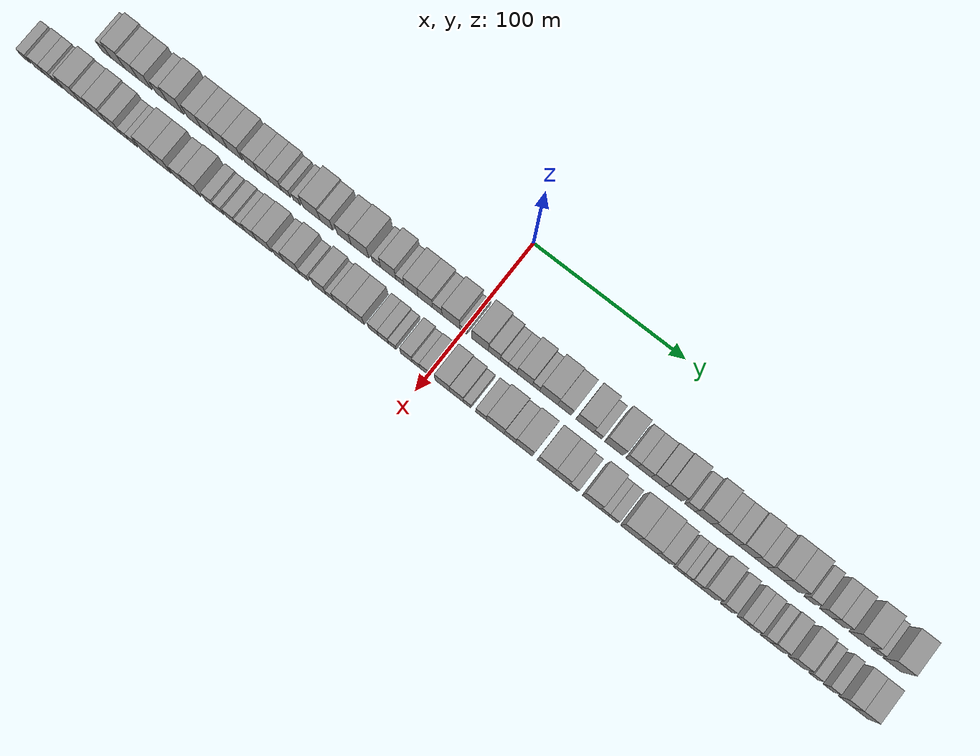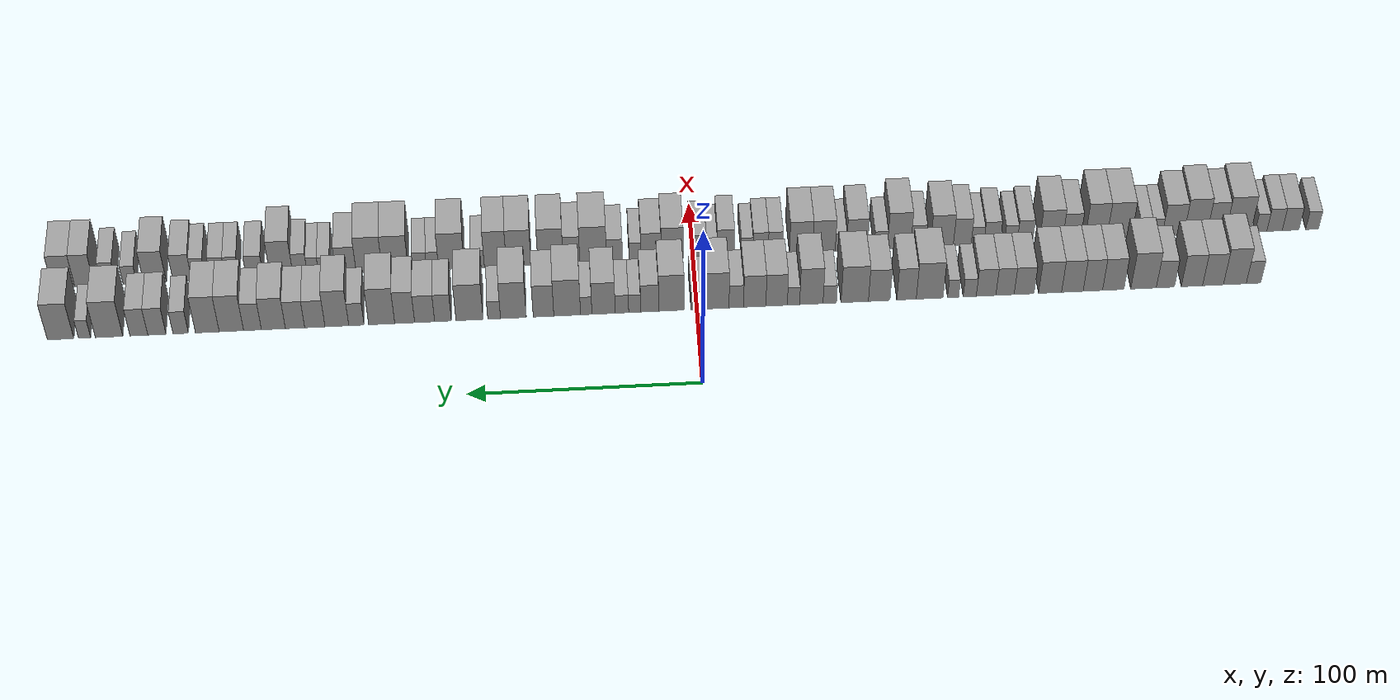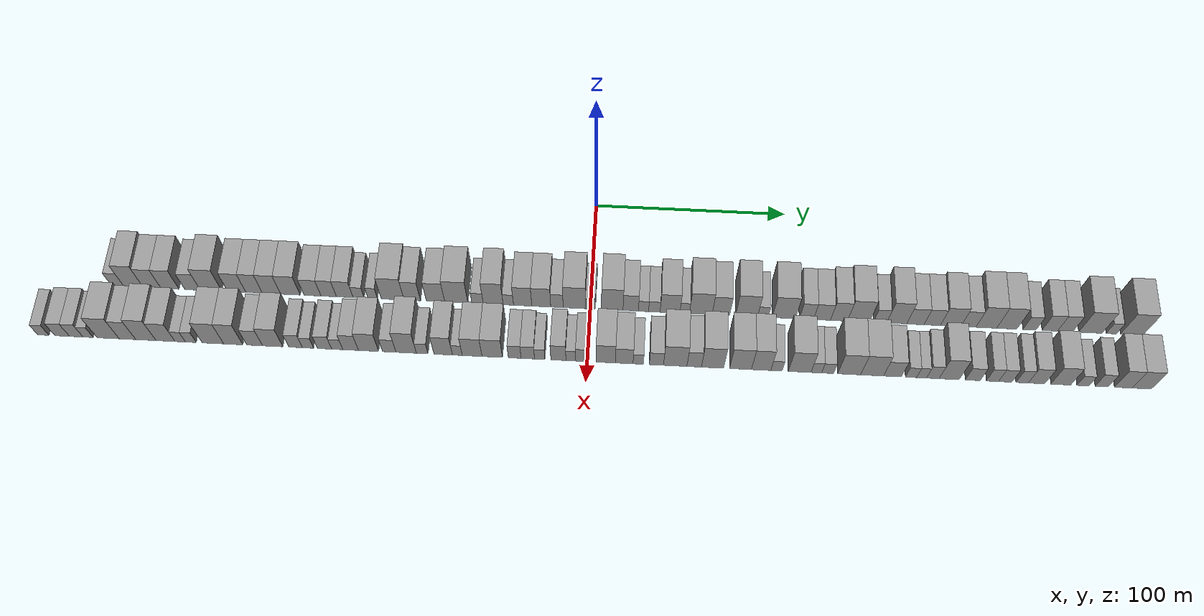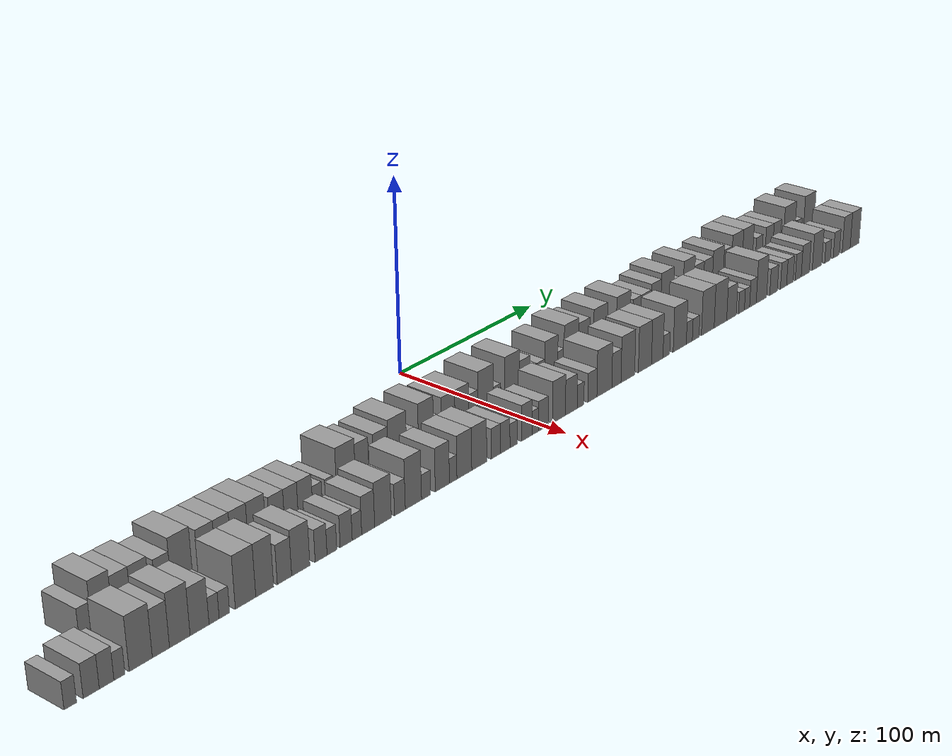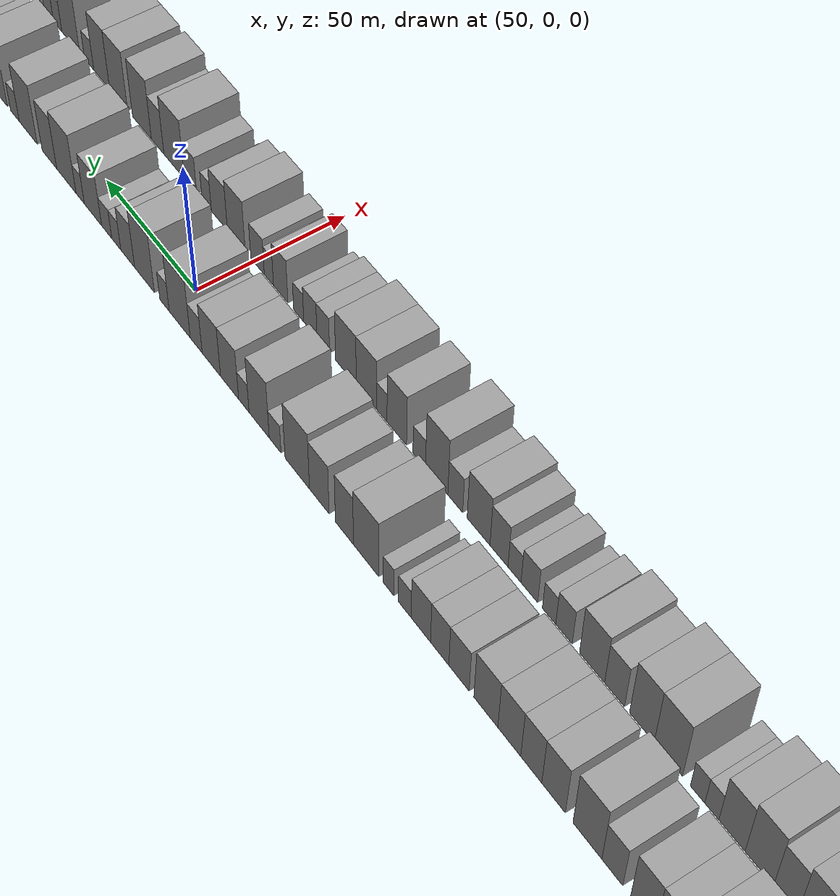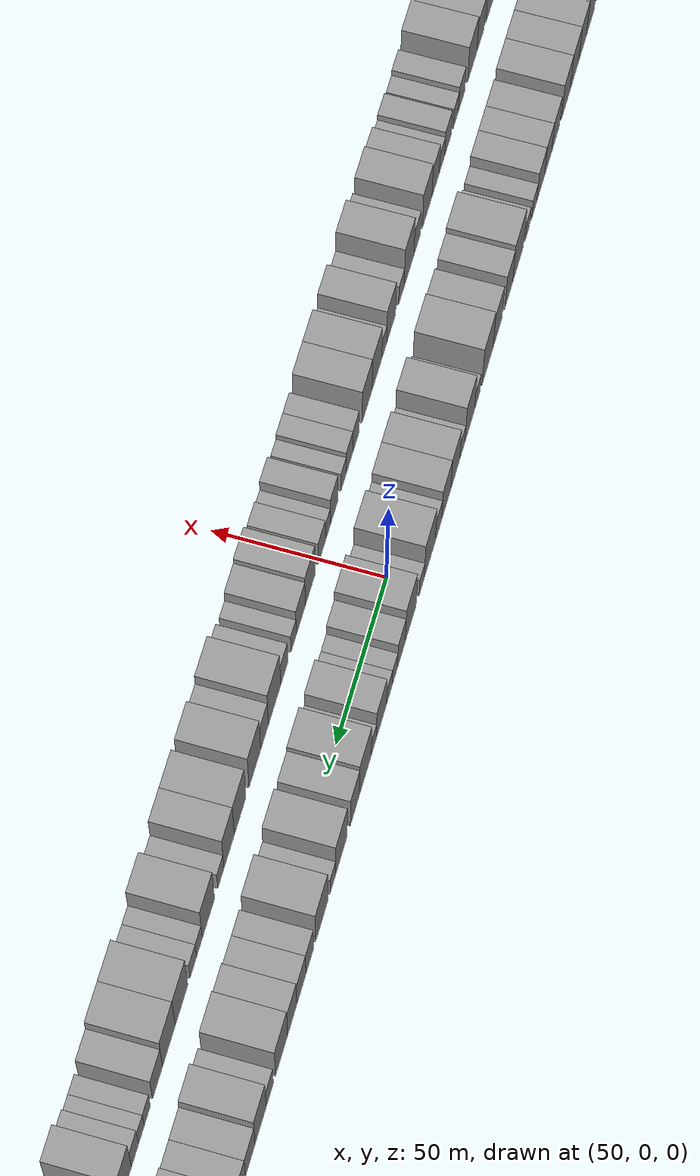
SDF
<sdf version="1.6">
 <world name="default">
  <scene>
   <sky><clouds><speed>12</speed></clouds></sky>
   <ambient>0.4 0.4 0.4 1</ambient>
   <background>0.7 0.7 0.7 1</background>
   <shadows>1</shadows>
  </scene>
  <gravity>0 0 -9.8066</gravity>
  <magnetic_field>6e-06 2.3e-05 -4.2e-05</magnetic_field>
  <physics default="0" name="default_physics" type="ode">
   <ode>
    <solver>
     <type>quick</type>
     <iters>10</iters>
     <sor>1.0</sor>
     <use_dynamic_moi_rescaling>0</use_dynamic_moi_rescaling>
    </solver>
    <constraints>
     <cfm>0</cfm>
     <erp>0.2</erp>
     <contact_max_correcting_vel>100</contact_max_correcting_vel>
     <contact_surface_layer>0.001</contact_surface_layer>
    </constraints>
   </ode>
   <max_step_size>0.004</max_step_size>
   <real_time_factor>1</real_time_factor>
   <real_time_update_rate>250</real_time_update_rate>
  </physics>
  <light name="sun" type="directional">
   <pose>0 0 10 0 0 0</pose>
   <diffuse>0.8 0.8 0.8 1</diffuse>
   <specular>0.2 0.2 0.2 1</specular>
   <attenuation>
    <range>1000</range>
    <constant>0.9</constant>
    <linear>0.01</linear>
    <quadratic>0.001</quadratic>
   </attenuation>
   <direction>-0.5 0.1 -0.9</direction>
  </light>
  <model name="building_1">
   <static>1</static>
   <pose>50.0000 -243.4653 0 0.000000 0.000000 0.000000</pose>
   <link name="link">
    <pose>0 0 7.50 0 0 0</pose>
    <collision name="collision"><geometry><box><size>20.0000 6.3565 15.0000</size></box></geometry></collision>
    <visual name="visual">
     <cast_shadows>0</cast_shadows>
     <geometry><box><size>20.0000 6.3565 15.0000</size></box></geometry>
     <material>
      <script>
       <uri>model://grey_wall/materials/scripts</uri>
       <uri>model://grey_wall/materials/textures</uri>
       <name>vrc/grey_wall</name>
      </script>
     </material>
    </visual>
   </link>
  </model>
  <model name="building_2">
   <static>1</static>
   <pose>50.0000 -235.2615 0 0.000000 0.000000 0.000000</pose>
   <link name="link">
    <pose>0 0 12.00 0 0 0</pose>
    <collision name="collision"><geometry><box><size>20.0000 10.0511 24.0000</size></box></geometry></collision>
    <visual name="visual">
     <cast_shadows>0</cast_shadows>
     <geometry><box><size>20.0000 10.0511 24.0000</size></box></geometry>
     <material>
      <script>
       <uri>model://grey_wall/materials/scripts</uri>
       <uri>model://grey_wall/materials/textures</uri>
       <name>vrc/grey_wall</name>
      </script>
     </material>
    </visual>
   </link>
  </model>
  <model name="building_3">
   <static>1</static>
   <pose>50.0000 -225.6346 0 0.000000 0.000000 0.000000</pose>
   <link name="link">
    <pose>0 0 10.50 0 0 0</pose>
    <collision name="collision"><geometry><box><size>20.0000 9.2027 21.0000</size></box></geometry></collision>
    <visual name="visual">
     <cast_shadows>0</cast_shadows>
     <geometry><box><size>20.0000 9.2027 21.0000</size></box></geometry>
     <material>
      <script>
       <uri>model://grey_wall/materials/scripts</uri>
       <uri>model://grey_wall/materials/textures</uri>
       <name>vrc/grey_wall</name>
      </script>
     </material>
    </visual>
   </link>
  </model>
  <model name="building_4">
   <static>1</static>
   <pose>50.0000 -216.3543 0 0.000000 0.000000 0.000000</pose>
   <link name="link">
    <pose>0 0 10.50 0 0 0</pose>
    <collision name="collision"><geometry><box><size>20.0000 9.3578 21.0000</size></box></geometry></collision>
    <visual name="visual">
     <cast_shadows>0</cast_shadows>
     <geometry><box><size>20.0000 9.3578 21.0000</size></box></geometry>
     <material>
      <script>
       <uri>model://grey_wall/materials/scripts</uri>
       <uri>model://grey_wall/materials/textures</uri>
       <name>vrc/grey_wall</name>
      </script>
     </material>
    </visual>
   </link>
  </model>
  <model name="building_5">
   <static>1</static>
   <pose>50.0000 -204.6761 0 0.000000 0.000000 0.000000</pose>
   <link name="link">
    <pose>0 0 9.00 0 0 0</pose>
    <collision name="collision"><geometry><box><size>20.0000 7.9984 18.0000</size></box></geometry></collision>
    <visual name="visual">
     <cast_shadows>0</cast_shadows>
     <geometry><box><size>20.0000 7.9984 18.0000</size></box></geometry>
     <material>
      <script>
       <uri>model://grey_wall/materials/scripts</uri>
       <uri>model://grey_wall/materials/textures</uri>
       <name>vrc/grey_wall</name>
      </script>
     </material>
    </visual>
   </link>
  </model>
  <model name="building_6">
   <static>1</static>
   <pose>50.0000 -195.0604 0 0.000000 0.000000 0.000000</pose>
   <link name="link">
    <pose>0 0 12.00 0 0 0</pose>
    <collision name="collision"><geometry><box><size>20.0000 11.2330 24.0000</size></box></geometry></collision>
    <visual name="visual">
     <cast_shadows>0</cast_shadows>
     <geometry><box><size>20.0000 11.2330 24.0000</size></box></geometry>
     <material>
      <script>
       <uri>model://grey_wall/materials/scripts</uri>
       <uri>model://grey_wall/materials/textures</uri>
       <name>vrc/grey_wall</name>
      </script>
     </material>
    </visual>
   </link>
  </model>
  <model name="building_7">
   <static>1</static>
   <pose>50.0000 -181.7462 0 0.000000 0.000000 0.000000</pose>
   <link name="link">
    <pose>0 0 10.50 0 0 0</pose>
    <collision name="collision"><geometry><box><size>20.0000 9.3955 21.0000</size></box></geometry></collision>
    <visual name="visual">
     <cast_shadows>0</cast_shadows>
     <geometry><box><size>20.0000 9.3955 21.0000</size></box></geometry>
     <material>
      <script>
       <uri>model://grey_wall/materials/scripts</uri>
       <uri>model://grey_wall/materials/textures</uri>
       <name>vrc/grey_wall</name>
      </script>
     </material>
    </visual>
   </link>
  </model>
  <model name="building_8">
   <static>1</static>
   <pose>50.0000 -172.7809 0 0.000000 0.000000 0.000000</pose>
   <link name="link">
    <pose>0 0 10.50 0 0 0</pose>
    <collision name="collision"><geometry><box><size>20.0000 8.5352 21.0000</size></box></geometry></collision>
    <visual name="visual">
     <cast_shadows>0</cast_shadows>
     <geometry><box><size>20.0000 8.5352 21.0000</size></box></geometry>
     <material>
      <script>
       <uri>model://grey_wall/materials/scripts</uri>
       <uri>model://grey_wall/materials/textures</uri>
       <name>vrc/grey_wall</name>
      </script>
     </material>
    </visual>
   </link>
  </model>
  <model name="building_9">
   <static>1</static>
   <pose>50.0000 -163.7845 0 0.000000 0.000000 0.000000</pose>
   <link name="link">
    <pose>0 0 10.50 0 0 0</pose>
    <collision name="collision"><geometry><box><size>20.0000 9.4576 21.0000</size></box></geometry></collision>
    <visual name="visual">
     <cast_shadows>0</cast_shadows>
     <geometry><box><size>20.0000 9.4576 21.0000</size></box></geometry>
     <material>
      <script>
       <uri>model://grey_wall/materials/scripts</uri>
       <uri>model://grey_wall/materials/textures</uri>
       <name>vrc/grey_wall</name>
      </script>
     </material>
    </visual>
   </link>
  </model>
  <model name="building_10">
   <static>1</static>
   <pose>50.0000 -154.0091 0 0.000000 0.000000 0.000000</pose>
   <link name="link">
    <pose>0 0 10.50 0 0 0</pose>
    <collision name="collision"><geometry><box><size>20.0000 10.0933 21.0000</size></box></geometry></collision>
    <visual name="visual">
     <cast_shadows>0</cast_shadows>
     <geometry><box><size>20.0000 10.0933 21.0000</size></box></geometry>
     <material>
      <script>
       <uri>model://grey_wall/materials/scripts</uri>
       <uri>model://grey_wall/materials/textures</uri>
       <name>vrc/grey_wall</name>
      </script>
     </material>
    </visual>
   </link>
  </model>
  <model name="building_11">
   <static>1</static>
   <pose>50.0000 -142.6067 0 0.000000 0.000000 0.000000</pose>
   <link name="link">
    <pose>0 0 9.00 0 0 0</pose>
    <collision name="collision"><geometry><box><size>20.0000 8.7116 18.0000</size></box></geometry></collision>
    <visual name="visual">
     <cast_shadows>0</cast_shadows>
     <geometry><box><size>20.0000 8.7116 18.0000</size></box></geometry>
     <material>
      <script>
       <uri>model://grey_wall/materials/scripts</uri>
       <uri>model://grey_wall/materials/textures</uri>
       <name>vrc/grey_wall</name>
      </script>
     </material>
    </visual>
   </link>
  </model>
  <model name="building_12">
   <static>1</static>
   <pose>50.0000 -134.2623 0 0.000000 0.000000 0.000000</pose>
   <link name="link">
    <pose>0 0 9.00 0 0 0</pose>
    <collision name="collision"><geometry><box><size>20.0000 7.9771 18.0000</size></box></geometry></collision>
    <visual name="visual">
     <cast_shadows>0</cast_shadows>
     <geometry><box><size>20.0000 7.9771 18.0000</size></box></geometry>
     <material>
      <script>
       <uri>model://grey_wall/materials/scripts</uri>
       <uri>model://grey_wall/materials/textures</uri>
       <name>vrc/grey_wall</name>
      </script>
     </material>
    </visual>
   </link>
  </model>
  <model name="building_13">
   <static>1</static>
   <pose>50.0000 -125.9835 0 0.000000 0.000000 0.000000</pose>
   <link name="link">
    <pose>0 0 9.00 0 0 0</pose>
    <collision name="collision"><geometry><box><size>20.0000 8.5806 18.0000</size></box></geometry></collision>
    <visual name="visual">
     <cast_shadows>0</cast_shadows>
     <geometry><box><size>20.0000 8.5806 18.0000</size></box></geometry>
     <material>
      <script>
       <uri>model://grey_wall/materials/scripts</uri>
       <uri>model://grey_wall/materials/textures</uri>
       <name>vrc/grey_wall</name>
      </script>
     </material>
    </visual>
   </link>
  </model>
  <model name="building_14">
   <static>1</static>
   <pose>50.0000 -118.8375 0 0.000000 0.000000 0.000000</pose>
   <link name="link">
    <pose>0 0 6.00 0 0 0</pose>
    <collision name="collision"><geometry><box><size>20.0000 5.7114 12.0000</size></box></geometry></collision>
    <visual name="visual">
     <cast_shadows>0</cast_shadows>
     <geometry><box><size>20.0000 5.7114 12.0000</size></box></geometry>
     <material>
      <script>
       <uri>model://grey_wall/materials/scripts</uri>
       <uri>model://grey_wall/materials/textures</uri>
       <name>vrc/grey_wall</name>
      </script>
     </material>
    </visual>
   </link>
  </model>
  <model name="building_15">
   <static>1</static>
   <pose>50.0000 -111.5586 0 0.000000 0.000000 0.000000</pose>
   <link name="link">
    <pose>0 0 6.00 0 0 0</pose>
    <collision name="collision"><geometry><box><size>20.0000 4.8464 12.0000</size></box></geometry></collision>
    <visual name="visual">
     <cast_shadows>0</cast_shadows>
     <geometry><box><size>20.0000 4.8464 12.0000</size></box></geometry>
     <material>
      <script>
       <uri>model://grey_wall/materials/scripts</uri>
       <uri>model://grey_wall/materials/textures</uri>
       <name>vrc/grey_wall</name>
      </script>
     </material>
    </visual>
   </link>
  </model>
  <model name="building_16">
   <static>1</static>
   <pose>50.0000 -101.2901 0 0.000000 0.000000 0.000000</pose>
   <link name="link">
    <pose>0 0 12.00 0 0 0</pose>
    <collision name="collision"><geometry><box><size>20.0000 11.6907 24.0000</size></box></geometry></collision>
    <visual name="visual">
     <cast_shadows>0</cast_shadows>
     <geometry><box><size>20.0000 11.6907 24.0000</size></box></geometry>
     <material>
      <script>
       <uri>model://grey_wall/materials/scripts</uri>
       <uri>model://grey_wall/materials/textures</uri>
       <name>vrc/grey_wall</name>
      </script>
     </material>
    </visual>
   </link>
  </model>
  <model name="building_17">
   <static>1</static>
   <pose>50.0000 -91.2035 0 0.000000 0.000000 0.000000</pose>
   <link name="link">
    <pose>0 0 10.50 0 0 0</pose>
    <collision name="collision"><geometry><box><size>20.0000 8.4825 21.0000</size></box></geometry></collision>
    <visual name="visual">
     <cast_shadows>0</cast_shadows>
     <geometry><box><size>20.0000 8.4825 21.0000</size></box></geometry>
     <material>
      <script>
       <uri>model://grey_wall/materials/scripts</uri>
       <uri>model://grey_wall/materials/textures</uri>
       <name>vrc/grey_wall</name>
      </script>
     </material>
    </visual>
   </link>
  </model>
  <model name="building_18">
   <static>1</static>
   <pose>50.0000 -79.2576 0 0.000000 0.000000 0.000000</pose>
   <link name="link">
    <pose>0 0 10.50 0 0 0</pose>
    <collision name="collision"><geometry><box><size>20.0000 9.4094 21.0000</size></box></geometry></collision>
    <visual name="visual">
     <cast_shadows>0</cast_shadows>
     <geometry><box><size>20.0000 9.4094 21.0000</size></box></geometry>
     <material>
      <script>
       <uri>model://grey_wall/materials/scripts</uri>
       <uri>model://grey_wall/materials/textures</uri>
       <name>vrc/grey_wall</name>
      </script>
     </material>
    </visual>
   </link>
  </model>
  <model name="building_19">
   <static>1</static>
   <pose>50.0000 -68.5814 0 0.000000 0.000000 0.000000</pose>
   <link name="link">
    <pose>0 0 12.00 0 0 0</pose>
    <collision name="collision"><geometry><box><size>20.0000 11.9430 24.0000</size></box></geometry></collision>
    <visual name="visual">
     <cast_shadows>0</cast_shadows>
     <geometry><box><size>20.0000 11.9430 24.0000</size></box></geometry>
     <material>
      <script>
       <uri>model://grey_wall/materials/scripts</uri>
       <uri>model://grey_wall/materials/textures</uri>
       <name>vrc/grey_wall</name>
      </script>
     </material>
    </visual>
   </link>
  </model>
  <model name="building_20">
   <static>1</static>
   <pose>50.0000 -57.6788 0 0.000000 0.000000 0.000000</pose>
   <link name="link">
    <pose>0 0 6.00 0 0 0</pose>
    <collision name="collision"><geometry><box><size>20.0000 5.8621 12.0000</size></box></geometry></collision>
    <visual name="visual">
     <cast_shadows>0</cast_shadows>
     <geometry><box><size>20.0000 5.8621 12.0000</size></box></geometry>
     <material>
      <script>
       <uri>model://grey_wall/materials/scripts</uri>
       <uri>model://grey_wall/materials/textures</uri>
       <name>vrc/grey_wall</name>
      </script>
     </material>
    </visual>
   </link>
  </model>
  <model name="building_21">
   <static>1</static>
   <pose>50.0000 -49.6550 0 0.000000 0.000000 0.000000</pose>
   <link name="link">
    <pose>0 0 12.00 0 0 0</pose>
    <collision name="collision"><geometry><box><size>20.0000 10.1855 24.0000</size></box></geometry></collision>
    <visual name="visual">
     <cast_shadows>0</cast_shadows>
     <geometry><box><size>20.0000 10.1855 24.0000</size></box></geometry>
     <material>
      <script>
       <uri>model://grey_wall/materials/scripts</uri>
       <uri>model://grey_wall/materials/textures</uri>
       <name>vrc/grey_wall</name>
      </script>
     </material>
    </visual>
   </link>
  </model>
  <model name="building_22">
   <static>1</static>
   <pose>50.0000 -41.8930 0 0.000000 0.000000 0.000000</pose>
   <link name="link">
    <pose>0 0 6.00 0 0 0</pose>
    <collision name="collision"><geometry><box><size>20.0000 5.3385 12.0000</size></box></geometry></collision>
    <visual name="visual">
     <cast_shadows>0</cast_shadows>
     <geometry><box><size>20.0000 5.3385 12.0000</size></box></geometry>
     <material>
      <script>
       <uri>model://grey_wall/materials/scripts</uri>
       <uri>model://grey_wall/materials/textures</uri>
       <name>vrc/grey_wall</name>
      </script>
     </material>
    </visual>
   </link>
  </model>
  <model name="building_23">
   <static>1</static>
   <pose>50.0000 -34.5507 0 0.000000 0.000000 0.000000</pose>
   <link name="link">
    <pose>0 0 10.50 0 0 0</pose>
    <collision name="collision"><geometry><box><size>20.0000 9.3463 21.0000</size></box></geometry></collision>
    <visual name="visual">
     <cast_shadows>0</cast_shadows>
     <geometry><box><size>20.0000 9.3463 21.0000</size></box></geometry>
     <material>
      <script>
       <uri>model://grey_wall/materials/scripts</uri>
       <uri>model://grey_wall/materials/textures</uri>
       <name>vrc/grey_wall</name>
      </script>
     </material>
    </visual>
   </link>
  </model>
  <model name="building_24">
   <static>1</static>
   <pose>50.0000 -25.0386 0 0.000000 0.000000 0.000000</pose>
   <link name="link">
    <pose>0 0 10.50 0 0 0</pose>
    <collision name="collision"><geometry><box><size>20.0000 9.6778 21.0000</size></box></geometry></collision>
    <visual name="visual">
     <cast_shadows>0</cast_shadows>
     <geometry><box><size>20.0000 9.6778 21.0000</size></box></geometry>
     <material>
      <script>
       <uri>model://grey_wall/materials/scripts</uri>
       <uri>model://grey_wall/materials/textures</uri>
       <name>vrc/grey_wall</name>
      </script>
     </material>
    </visual>
   </link>
  </model>
  <model name="building_25">
   <static>1</static>
   <pose>50.0000 -17.0260 0 0.000000 0.000000 0.000000</pose>
   <link name="link">
    <pose>0 0 7.50 0 0 0</pose>
    <collision name="collision"><geometry><box><size>20.0000 6.3474 15.0000</size></box></geometry></collision>
    <visual name="visual">
     <cast_shadows>0</cast_shadows>
     <geometry><box><size>20.0000 6.3474 15.0000</size></box></geometry>
     <material>
      <script>
       <uri>model://grey_wall/materials/scripts</uri>
       <uri>model://grey_wall/materials/textures</uri>
       <name>vrc/grey_wall</name>
      </script>
     </material>
    </visual>
   </link>
  </model>
  <model name="building_26">
   <static>1</static>
   <pose>50.0000 -8.1673 0 0.000000 0.000000 0.000000</pose>
   <link name="link">
    <pose>0 0 12.00 0 0 0</pose>
    <collision name="collision"><geometry><box><size>20.0000 11.3700 24.0000</size></box></geometry></collision>
    <visual name="visual">
     <cast_shadows>0</cast_shadows>
     <geometry><box><size>20.0000 11.3700 24.0000</size></box></geometry>
     <material>
      <script>
       <uri>model://grey_wall/materials/scripts</uri>
       <uri>model://grey_wall/materials/textures</uri>
       <name>vrc/grey_wall</name>
      </script>
     </material>
    </visual>
   </link>
  </model>
  <model name="building_27">
   <static>1</static>
   <pose>50.0000 0.0869 0 0.000000 0.000000 0.000000</pose>
   <link name="link">
    <pose>0 0 6.00 0 0 0</pose>
    <collision name="collision"><geometry><box><size>20.0000 5.1384 12.0000</size></box></geometry></collision>
    <visual name="visual">
     <cast_shadows>0</cast_shadows>
     <geometry><box><size>20.0000 5.1384 12.0000</size></box></geometry>
     <material>
      <script>
       <uri>model://grey_wall/materials/scripts</uri>
       <uri>model://grey_wall/materials/textures</uri>
       <name>vrc/grey_wall</name>
      </script>
     </material>
    </visual>
   </link>
  </model>
  <model name="building_28">
   <static>1</static>
   <pose>50.0000 11.1717 0 0.000000 0.000000 0.000000</pose>
   <link name="link">
    <pose>0 0 12.00 0 0 0</pose>
    <collision name="collision"><geometry><box><size>20.0000 11.0312 24.0000</size></box></geometry></collision>
    <visual name="visual">
     <cast_shadows>0</cast_shadows>
     <geometry><box><size>20.0000 11.0312 24.0000</size></box></geometry>
     <material>
      <script>
       <uri>model://grey_wall/materials/scripts</uri>
       <uri>model://grey_wall/materials/textures</uri>
       <name>vrc/grey_wall</name>
      </script>
     </material>
    </visual>
   </link>
  </model>
  <model name="building_29">
   <static>1</static>
   <pose>50.0000 20.5993 0 0.000000 0.000000 0.000000</pose>
   <link name="link">
    <pose>0 0 9.00 0 0 0</pose>
    <collision name="collision"><geometry><box><size>20.0000 7.8240 18.0000</size></box></geometry></collision>
    <visual name="visual">
     <cast_shadows>0</cast_shadows>
     <geometry><box><size>20.0000 7.8240 18.0000</size></box></geometry>
     <material>
      <script>
       <uri>model://grey_wall/materials/scripts</uri>
       <uri>model://grey_wall/materials/textures</uri>
       <name>vrc/grey_wall</name>
      </script>
     </material>
    </visual>
   </link>
  </model>
  <model name="building_30">
   <static>1</static>
   <pose>50.0000 27.1070 0 0.000000 0.000000 0.000000</pose>
   <link name="link">
    <pose>0 0 6.00 0 0 0</pose>
    <collision name="collision"><geometry><box><size>20.0000 5.1913 12.0000</size></box></geometry></collision>
    <visual name="visual">
     <cast_shadows>0</cast_shadows>
     <geometry><box><size>20.0000 5.1913 12.0000</size></box></geometry>
     <material>
      <script>
       <uri>model://grey_wall/materials/scripts</uri>
       <uri>model://grey_wall/materials/textures</uri>
       <name>vrc/grey_wall</name>
      </script>
     </material>
    </visual>
   </link>
  </model>
  <model name="building_31">
   <static>1</static>
   <pose>50.0000 32.6259 0 0.000000 0.000000 0.000000</pose>
   <link name="link">
    <pose>0 0 6.00 0 0 0</pose>
    <collision name="collision"><geometry><box><size>20.0000 5.8464 12.0000</size></box></geometry></collision>
    <visual name="visual">
     <cast_shadows>0</cast_shadows>
     <geometry><box><size>20.0000 5.8464 12.0000</size></box></geometry>
     <material>
      <script>
       <uri>model://grey_wall/materials/scripts</uri>
       <uri>model://grey_wall/materials/textures</uri>
       <name>vrc/grey_wall</name>
      </script>
     </material>
    </visual>
   </link>
  </model>
  <model name="building_32">
   <static>1</static>
   <pose>50.0000 40.5985 0 0.000000 0.000000 0.000000</pose>
   <link name="link">
    <pose>0 0 10.50 0 0 0</pose>
    <collision name="collision"><geometry><box><size>20.0000 10.0989 21.0000</size></box></geometry></collision>
    <visual name="visual">
     <cast_shadows>0</cast_shadows>
     <geometry><box><size>20.0000 10.0989 21.0000</size></box></geometry>
     <material>
      <script>
       <uri>model://grey_wall/materials/scripts</uri>
       <uri>model://grey_wall/materials/textures</uri>
       <name>vrc/grey_wall</name>
      </script>
     </material>
    </visual>
   </link>
  </model>
  <model name="building_33">
   <static>1</static>
   <pose>50.0000 48.1005 0 0.000000 0.000000 0.000000</pose>
   <link name="link">
    <pose>0 0 6.00 0 0 0</pose>
    <collision name="collision"><geometry><box><size>20.0000 4.9049 12.0000</size></box></geometry></collision>
    <visual name="visual">
     <cast_shadows>0</cast_shadows>
     <geometry><box><size>20.0000 4.9049 12.0000</size></box></geometry>
     <material>
      <script>
       <uri>model://grey_wall/materials/scripts</uri>
       <uri>model://grey_wall/materials/textures</uri>
       <name>vrc/grey_wall</name>
      </script>
     </material>
    </visual>
   </link>
  </model>
  <model name="building_34">
   <static>1</static>
   <pose>50.0000 56.3387 0 0.000000 0.000000 0.000000</pose>
   <link name="link">
    <pose>0 0 12.00 0 0 0</pose>
    <collision name="collision"><geometry><box><size>20.0000 11.5715 24.0000</size></box></geometry></collision>
    <visual name="visual">
     <cast_shadows>0</cast_shadows>
     <geometry><box><size>20.0000 11.5715 24.0000</size></box></geometry>
     <material>
      <script>
       <uri>model://grey_wall/materials/scripts</uri>
       <uri>model://grey_wall/materials/textures</uri>
       <name>vrc/grey_wall</name>
      </script>
     </material>
    </visual>
   </link>
  </model>
  <model name="building_35">
   <static>1</static>
   <pose>50.0000 66.5732 0 0.000000 0.000000 0.000000</pose>
   <link name="link">
    <pose>0 0 10.50 0 0 0</pose>
    <collision name="collision"><geometry><box><size>20.0000 8.8975 21.0000</size></box></geometry></collision>
    <visual name="visual">
     <cast_shadows>0</cast_shadows>
     <geometry><box><size>20.0000 8.8975 21.0000</size></box></geometry>
     <material>
      <script>
       <uri>model://grey_wall/materials/scripts</uri>
       <uri>model://grey_wall/materials/textures</uri>
       <name>vrc/grey_wall</name>
      </script>
     </material>
    </visual>
   </link>
  </model>
  <model name="building_36">
   <static>1</static>
   <pose>50.0000 79.5994 0 0.000000 0.000000 0.000000</pose>
   <link name="link">
    <pose>0 0 12.00 0 0 0</pose>
    <collision name="collision"><geometry><box><size>20.0000 11.1550 24.0000</size></box></geometry></collision>
    <visual name="visual">
     <cast_shadows>0</cast_shadows>
     <geometry><box><size>20.0000 11.1550 24.0000</size></box></geometry>
     <material>
      <script>
       <uri>model://grey_wall/materials/scripts</uri>
       <uri>model://grey_wall/materials/textures</uri>
       <name>vrc/grey_wall</name>
      </script>
     </material>
    </visual>
   </link>
  </model>
  <model name="building_37">
   <static>1</static>
   <pose>50.0000 87.9173 0 0.000000 0.000000 0.000000</pose>
   <link name="link">
    <pose>0 0 6.00 0 0 0</pose>
    <collision name="collision"><geometry><box><size>20.0000 5.4807 12.0000</size></box></geometry></collision>
    <visual name="visual">
     <cast_shadows>0</cast_shadows>
     <geometry><box><size>20.0000 5.4807 12.0000</size></box></geometry>
     <material>
      <script>
       <uri>model://grey_wall/materials/scripts</uri>
       <uri>model://grey_wall/materials/textures</uri>
       <name>vrc/grey_wall</name>
      </script>
     </material>
    </visual>
   </link>
  </model>
  <model name="building_38">
   <static>1</static>
   <pose>50.0000 98.5186 0 0.000000 0.000000 0.000000</pose>
   <link name="link">
    <pose>0 0 12.00 0 0 0</pose>
    <collision name="collision"><geometry><box><size>20.0000 11.7219 24.0000</size></box></geometry></collision>
    <visual name="visual">
     <cast_shadows>0</cast_shadows>
     <geometry><box><size>20.0000 11.7219 24.0000</size></box></geometry>
     <material>
      <script>
       <uri>model://grey_wall/materials/scripts</uri>
       <uri>model://grey_wall/materials/textures</uri>
       <name>vrc/grey_wall</name>
      </script>
     </material>
    </visual>
   </link>
  </model>
  <model name="building_39">
   <static>1</static>
   <pose>50.0000 109.9865 0 0.000000 0.000000 0.000000</pose>
   <link name="link">
    <pose>0 0 9.00 0 0 0</pose>
    <collision name="collision"><geometry><box><size>20.0000 7.2139 18.0000</size></box></geometry></collision>
    <visual name="visual">
     <cast_shadows>0</cast_shadows>
     <geometry><box><size>20.0000 7.2139 18.0000</size></box></geometry>
     <material>
      <script>
       <uri>model://grey_wall/materials/scripts</uri>
       <uri>model://grey_wall/materials/textures</uri>
       <name>vrc/grey_wall</name>
      </script>
     </material>
    </visual>
   </link>
  </model>
  <model name="building_40">
   <static>1</static>
   <pose>50.0000 117.9040 0 0.000000 0.000000 0.000000</pose>
   <link name="link">
    <pose>0 0 9.00 0 0 0</pose>
    <collision name="collision"><geometry><box><size>20.0000 8.6211 18.0000</size></box></geometry></collision>
    <visual name="visual">
     <cast_shadows>0</cast_shadows>
     <geometry><box><size>20.0000 8.6211 18.0000</size></box></geometry>
     <material>
      <script>
       <uri>model://grey_wall/materials/scripts</uri>
       <uri>model://grey_wall/materials/textures</uri>
       <name>vrc/grey_wall</name>
      </script>
     </material>
    </visual>
   </link>
  </model>
  <model name="building_41">
   <static>1</static>
   <pose>50.0000 126.5039 0 0.000000 0.000000 0.000000</pose>
   <link name="link">
    <pose>0 0 10.50 0 0 0</pose>
    <collision name="collision"><geometry><box><size>20.0000 8.5786 21.0000</size></box></geometry></collision>
    <visual name="visual">
     <cast_shadows>0</cast_shadows>
     <geometry><box><size>20.0000 8.5786 21.0000</size></box></geometry>
     <material>
      <script>
       <uri>model://grey_wall/materials/scripts</uri>
       <uri>model://grey_wall/materials/textures</uri>
       <name>vrc/grey_wall</name>
      </script>
     </material>
    </visual>
   </link>
  </model>
  <model name="building_42">
   <static>1</static>
   <pose>50.0000 136.4017 0 0.000000 0.000000 0.000000</pose>
   <link name="link">
    <pose>0 0 12.00 0 0 0</pose>
    <collision name="collision"><geometry><box><size>20.0000 11.2170 24.0000</size></box></geometry></collision>
    <visual name="visual">
     <cast_shadows>0</cast_shadows>
     <geometry><box><size>20.0000 11.2170 24.0000</size></box></geometry>
     <material>
      <script>
       <uri>model://grey_wall/materials/scripts</uri>
       <uri>model://grey_wall/materials/textures</uri>
       <name>vrc/grey_wall</name>
      </script>
     </material>
    </visual>
   </link>
  </model>
  <model name="building_43">
   <static>1</static>
   <pose>50.0000 147.2961 0 0.000000 0.000000 0.000000</pose>
   <link name="link">
    <pose>0 0 7.50 0 0 0</pose>
    <collision name="collision"><geometry><box><size>20.0000 6.5718 15.0000</size></box></geometry></collision>
    <visual name="visual">
     <cast_shadows>0</cast_shadows>
     <geometry><box><size>20.0000 6.5718 15.0000</size></box></geometry>
     <material>
      <script>
       <uri>model://grey_wall/materials/scripts</uri>
       <uri>model://grey_wall/materials/textures</uri>
       <name>vrc/grey_wall</name>
      </script>
     </material>
    </visual>
   </link>
  </model>
  <model name="building_44">
   <static>1</static>
   <pose>50.0000 155.6939 0 0.000000 0.000000 0.000000</pose>
   <link name="link">
    <pose>0 0 12.00 0 0 0</pose>
    <collision name="collision"><geometry><box><size>20.0000 10.2238 24.0000</size></box></geometry></collision>
    <visual name="visual">
     <cast_shadows>0</cast_shadows>
     <geometry><box><size>20.0000 10.2238 24.0000</size></box></geometry>
     <material>
      <script>
       <uri>model://grey_wall/materials/scripts</uri>
       <uri>model://grey_wall/materials/textures</uri>
       <name>vrc/grey_wall</name>
      </script>
     </material>
    </visual>
   </link>
  </model>
  <model name="building_45">
   <static>1</static>
   <pose>50.0000 165.1732 0 0.000000 0.000000 0.000000</pose>
   <link name="link">
    <pose>0 0 9.00 0 0 0</pose>
    <collision name="collision"><geometry><box><size>20.0000 8.7346 18.0000</size></box></geometry></collision>
    <visual name="visual">
     <cast_shadows>0</cast_shadows>
     <geometry><box><size>20.0000 8.7346 18.0000</size></box></geometry>
     <material>
      <script>
       <uri>model://grey_wall/materials/scripts</uri>
       <uri>model://grey_wall/materials/textures</uri>
       <name>vrc/grey_wall</name>
      </script>
     </material>
    </visual>
   </link>
  </model>
  <model name="building_46">
   <static>1</static>
   <pose>50.0000 173.6865 0 0.000000 0.000000 0.000000</pose>
   <link name="link">
    <pose>0 0 9.00 0 0 0</pose>
    <collision name="collision"><geometry><box><size>20.0000 8.2920 18.0000</size></box></geometry></collision>
    <visual name="visual">
     <cast_shadows>0</cast_shadows>
     <geometry><box><size>20.0000 8.2920 18.0000</size></box></geometry>
     <material>
      <script>
       <uri>model://grey_wall/materials/scripts</uri>
       <uri>model://grey_wall/materials/textures</uri>
       <name>vrc/grey_wall</name>
      </script>
     </material>
    </visual>
   </link>
  </model>
  <model name="building_47">
   <static>1</static>
   <pose>50.0000 182.9807 0 0.000000 0.000000 0.000000</pose>
   <link name="link">
    <pose>0 0 10.50 0 0 0</pose>
    <collision name="collision"><geometry><box><size>20.0000 10.2964 21.0000</size></box></geometry></collision>
    <visual name="visual">
     <cast_shadows>0</cast_shadows>
     <geometry><box><size>20.0000 10.2964 21.0000</size></box></geometry>
     <material>
      <script>
       <uri>model://grey_wall/materials/scripts</uri>
       <uri>model://grey_wall/materials/textures</uri>
       <name>vrc/grey_wall</name>
      </script>
     </material>
    </visual>
   </link>
  </model>
  <model name="building_48">
   <static>1</static>
   <pose>50.0000 191.9526 0 0.000000 0.000000 0.000000</pose>
   <link name="link">
    <pose>0 0 9.00 0 0 0</pose>
    <collision name="collision"><geometry><box><size>20.0000 7.6473 18.0000</size></box></geometry></collision>
    <visual name="visual">
     <cast_shadows>0</cast_shadows>
     <geometry><box><size>20.0000 7.6473 18.0000</size></box></geometry>
     <material>
      <script>
       <uri>model://grey_wall/materials/scripts</uri>
       <uri>model://grey_wall/materials/textures</uri>
       <name>vrc/grey_wall</name>
      </script>
     </material>
    </visual>
   </link>
  </model>
  <model name="building_49">
   <static>1</static>
   <pose>50.0000 201.0170 0 0.000000 0.000000 0.000000</pose>
   <link name="link">
    <pose>0 0 12.00 0 0 0</pose>
    <collision name="collision"><geometry><box><size>20.0000 10.4815 24.0000</size></box></geometry></collision>
    <visual name="visual">
     <cast_shadows>0</cast_shadows>
     <geometry><box><size>20.0000 10.4815 24.0000</size></box></geometry>
     <material>
      <script>
       <uri>model://grey_wall/materials/scripts</uri>
       <uri>model://grey_wall/materials/textures</uri>
       <name>vrc/grey_wall</name>
      </script>
     </material>
    </visual>
   </link>
  </model>
  <model name="building_50">
   <static>1</static>
   <pose>50.0000 211.3477 0 0.000000 0.000000 0.000000</pose>
   <link name="link">
    <pose>0 0 12.00 0 0 0</pose>
    <collision name="collision"><geometry><box><size>20.0000 10.1798 24.0000</size></box></geometry></collision>
    <visual name="visual">
     <cast_shadows>0</cast_shadows>
     <geometry><box><size>20.0000 10.1798 24.0000</size></box></geometry>
     <material>
      <script>
       <uri>model://grey_wall/materials/scripts</uri>
       <uri>model://grey_wall/materials/textures</uri>
       <name>vrc/grey_wall</name>
      </script>
     </material>
    </visual>
   </link>
  </model>
  <model name="building_51">
   <static>1</static>
   <pose>50.0000 222.7443 0 0.000000 0.000000 0.000000</pose>
   <link name="link">
    <pose>0 0 7.50 0 0 0</pose>
    <collision name="collision"><geometry><box><size>20.0000 6.6134 15.0000</size></box></geometry></collision>
    <visual name="visual">
     <cast_shadows>0</cast_shadows>
     <geometry><box><size>20.0000 6.6134 15.0000</size></box></geometry>
     <material>
      <script>
       <uri>model://grey_wall/materials/scripts</uri>
       <uri>model://grey_wall/materials/textures</uri>
       <name>vrc/grey_wall</name>
      </script>
     </material>
    </visual>
   </link>
  </model>
  <model name="building_52">
   <static>1</static>
   <pose>50.0000 232.9578 0 0.000000 0.000000 0.000000</pose>
   <link name="link">
    <pose>0 0 9.00 0 0 0</pose>
    <collision name="collision"><geometry><box><size>20.0000 7.8135 18.0000</size></box></geometry></collision>
    <visual name="visual">
     <cast_shadows>0</cast_shadows>
     <geometry><box><size>20.0000 7.8135 18.0000</size></box></geometry>
     <material>
      <script>
       <uri>model://grey_wall/materials/scripts</uri>
       <uri>model://grey_wall/materials/textures</uri>
       <name>vrc/grey_wall</name>
      </script>
     </material>
    </visual>
   </link>
  </model>
  <model name="building_53">
   <static>1</static>
   <pose>50.0000 240.6961 0 0.000000 0.000000 0.000000</pose>
   <link name="link">
    <pose>0 0 9.00 0 0 0</pose>
    <collision name="collision"><geometry><box><size>20.0000 7.6631 18.0000</size></box></geometry></collision>
    <visual name="visual">
     <cast_shadows>0</cast_shadows>
     <geometry><box><size>20.0000 7.6631 18.0000</size></box></geometry>
     <material>
      <script>
       <uri>model://grey_wall/materials/scripts</uri>
       <uri>model://grey_wall/materials/textures</uri>
       <name>vrc/grey_wall</name>
      </script>
     </material>
    </visual>
   </link>
  </model>
  <model name="building_54">
   <static>1</static>
   <pose>50.0000 253.4060 0 0.000000 0.000000 0.000000</pose>
   <link name="link">
    <pose>0 0 12.00 0 0 0</pose>
    <collision name="collision"><geometry><box><size>20.0000 11.7568 24.0000</size></box></geometry></collision>
    <visual name="visual">
     <cast_shadows>0</cast_shadows>
     <geometry><box><size>20.0000 11.7568 24.0000</size></box></geometry>
     <material>
      <script>
       <uri>model://grey_wall/materials/scripts</uri>
       <uri>model://grey_wall/materials/textures</uri>
       <name>vrc/grey_wall</name>
      </script>
     </material>
    </visual>
   </link>
  </model>
  <model name="building_55">
   <static>1</static>
   <pose>50.0000 263.8791 0 0.000000 0.000000 0.000000</pose>
   <link name="link">
    <pose>0 0 6.00 0 0 0</pose>
    <collision name="collision"><geometry><box><size>20.0000 5.1895 12.0000</size></box></geometry></collision>
    <visual name="visual">
     <cast_shadows>0</cast_shadows>
     <geometry><box><size>20.0000 5.1895 12.0000</size></box></geometry>
     <material>
      <script>
       <uri>model://grey_wall/materials/scripts</uri>
       <uri>model://grey_wall/materials/textures</uri>
       <name>vrc/grey_wall</name>
      </script>
     </material>
    </visual>
   </link>
  </model>
  <model name="building_56">
   <static>1</static>
   <pose>50.0000 274.1354 0 0.000000 0.000000 0.000000</pose>
   <link name="link">
    <pose>0 0 12.00 0 0 0</pose>
    <collision name="collision"><geometry><box><size>20.0000 11.3231 24.0000</size></box></geometry></collision>
    <visual name="visual">
     <cast_shadows>0</cast_shadows>
     <geometry><box><size>20.0000 11.3231 24.0000</size></box></geometry>
     <material>
      <script>
       <uri>model://grey_wall/materials/scripts</uri>
       <uri>model://grey_wall/materials/textures</uri>
       <name>vrc/grey_wall</name>
      </script>
     </material>
    </visual>
   </link>
  </model>
  <model name="building_57">
   <static>1</static>
   <pose>79.0000 -275.1417 0 0.000000 0.000000 0.000000</pose>
   <link name="link">
    <pose>0 0 6.00 0 0 0</pose>
    <collision name="collision"><geometry><box><size>20.0000 5.7165 12.0000</size></box></geometry></collision>
    <visual name="visual">
     <cast_shadows>0</cast_shadows>
     <geometry><box><size>20.0000 5.7165 12.0000</size></box></geometry>
     <material>
      <script>
       <uri>model://grey_wall/materials/scripts</uri>
       <uri>model://grey_wall/materials/textures</uri>
       <name>vrc/grey_wall</name>
      </script>
     </material>
    </visual>
   </link>
  </model>
  <model name="building_58">
   <static>1</static>
   <pose>79.0000 -265.5435 0 0.000000 0.000000 0.000000</pose>
   <link name="link">
    <pose>0 0 7.50 0 0 0</pose>
    <collision name="collision"><geometry><box><size>20.0000 7.4801 15.0000</size></box></geometry></collision>
    <visual name="visual">
     <cast_shadows>0</cast_shadows>
     <geometry><box><size>20.0000 7.4801 15.0000</size></box></geometry>
     <material>
      <script>
       <uri>model://grey_wall/materials/scripts</uri>
       <uri>model://grey_wall/materials/textures</uri>
       <name>vrc/grey_wall</name>
      </script>
     </material>
    </visual>
   </link>
  </model>
  <model name="building_59">
   <static>1</static>
   <pose>79.0000 -258.3628 0 0.000000 0.000000 0.000000</pose>
   <link name="link">
    <pose>0 0 7.50 0 0 0</pose>
    <collision name="collision"><geometry><box><size>20.0000 6.8813 15.0000</size></box></geometry></collision>
    <visual name="visual">
     <cast_shadows>0</cast_shadows>
     <geometry><box><size>20.0000 6.8813 15.0000</size></box></geometry>
     <material>
      <script>
       <uri>model://grey_wall/materials/scripts</uri>
       <uri>model://grey_wall/materials/textures</uri>
       <name>vrc/grey_wall</name>
      </script>
     </material>
    </visual>
   </link>
  </model>
  <model name="building_60">
   <static>1</static>
   <pose>79.0000 -252.3158 0 0.000000 0.000000 0.000000</pose>
   <link name="link">
    <pose>0 0 6.00 0 0 0</pose>
    <collision name="collision"><geometry><box><size>20.0000 5.2128 12.0000</size></box></geometry></collision>
    <visual name="visual">
     <cast_shadows>0</cast_shadows>
     <geometry><box><size>20.0000 5.2128 12.0000</size></box></geometry>
     <material>
      <script>
       <uri>model://grey_wall/materials/scripts</uri>
       <uri>model://grey_wall/materials/textures</uri>
       <name>vrc/grey_wall</name>
      </script>
     </material>
    </visual>
   </link>
  </model>
  <model name="building_61">
   <static>1</static>
   <pose>79.0000 -242.0895 0 0.000000 0.000000 0.000000</pose>
   <link name="link">
    <pose>0 0 12.00 0 0 0</pose>
    <collision name="collision"><geometry><box><size>20.0000 11.2398 24.0000</size></box></geometry></collision>
    <visual name="visual">
     <cast_shadows>0</cast_shadows>
     <geometry><box><size>20.0000 11.2398 24.0000</size></box></geometry>
     <material>
      <script>
       <uri>model://grey_wall/materials/scripts</uri>
       <uri>model://grey_wall/materials/textures</uri>
       <name>vrc/grey_wall</name>
      </script>
     </material>
    </visual>
   </link>
  </model>
  <model name="building_62">
   <static>1</static>
   <pose>79.0000 -232.2515 0 0.000000 0.000000 0.000000</pose>
   <link name="link">
    <pose>0 0 10.50 0 0 0</pose>
    <collision name="collision"><geometry><box><size>20.0000 8.4360 21.0000</size></box></geometry></collision>
    <visual name="visual">
     <cast_shadows>0</cast_shadows>
     <geometry><box><size>20.0000 8.4360 21.0000</size></box></geometry>
     <material>
      <script>
       <uri>model://grey_wall/materials/scripts</uri>
       <uri>model://grey_wall/materials/textures</uri>
       <name>vrc/grey_wall</name>
      </script>
     </material>
    </visual>
   </link>
  </model>
  <model name="building_63">
   <static>1</static>
   <pose>79.0000 -222.8602 0 0.000000 0.000000 0.000000</pose>
   <link name="link">
    <pose>0 0 12.00 0 0 0</pose>
    <collision name="collision"><geometry><box><size>20.0000 10.3467 24.0000</size></box></geometry></collision>
    <visual name="visual">
     <cast_shadows>0</cast_shadows>
     <geometry><box><size>20.0000 10.3467 24.0000</size></box></geometry>
     <material>
      <script>
       <uri>model://grey_wall/materials/scripts</uri>
       <uri>model://grey_wall/materials/textures</uri>
       <name>vrc/grey_wall</name>
      </script>
     </material>
    </visual>
   </link>
  </model>
  <model name="building_64">
   <static>1</static>
   <pose>79.0000 -212.8440 0 0.000000 0.000000 0.000000</pose>
   <link name="link">
    <pose>0 0 10.50 0 0 0</pose>
    <collision name="collision"><geometry><box><size>20.0000 9.6857 21.0000</size></box></geometry></collision>
    <visual name="visual">
     <cast_shadows>0</cast_shadows>
     <geometry><box><size>20.0000 9.6857 21.0000</size></box></geometry>
     <material>
      <script>
       <uri>model://grey_wall/materials/scripts</uri>
       <uri>model://grey_wall/materials/textures</uri>
       <name>vrc/grey_wall</name>
      </script>
     </material>
    </visual>
   </link>
  </model>
  <model name="building_65">
   <static>1</static>
   <pose>79.0000 -205.3781 0 0.000000 0.000000 0.000000</pose>
   <link name="link">
    <pose>0 0 6.00 0 0 0</pose>
    <collision name="collision"><geometry><box><size>20.0000 5.2461 12.0000</size></box></geometry></collision>
    <visual name="visual">
     <cast_shadows>0</cast_shadows>
     <geometry><box><size>20.0000 5.2461 12.0000</size></box></geometry>
     <material>
      <script>
       <uri>model://grey_wall/materials/scripts</uri>
       <uri>model://grey_wall/materials/textures</uri>
       <name>vrc/grey_wall</name>
      </script>
     </material>
    </visual>
   </link>
  </model>
  <model name="building_66">
   <static>1</static>
   <pose>79.0000 -200.0155 0 0.000000 0.000000 0.000000</pose>
   <link name="link">
    <pose>0 0 6.00 0 0 0</pose>
    <collision name="collision"><geometry><box><size>20.0000 5.4791 12.0000</size></box></geometry></collision>
    <visual name="visual">
     <cast_shadows>0</cast_shadows>
     <geometry><box><size>20.0000 5.4791 12.0000</size></box></geometry>
     <material>
      <script>
       <uri>model://grey_wall/materials/scripts</uri>
       <uri>model://grey_wall/materials/textures</uri>
       <name>vrc/grey_wall</name>
      </script>
     </material>
    </visual>
   </link>
  </model>
  <model name="building_67">
   <static>1</static>
   <pose>79.0000 -188.7970 0 0.000000 0.000000 0.000000</pose>
   <link name="link">
    <pose>0 0 12.00 0 0 0</pose>
    <collision name="collision"><geometry><box><size>20.0000 10.9581 24.0000</size></box></geometry></collision>
    <visual name="visual">
     <cast_shadows>0</cast_shadows>
     <geometry><box><size>20.0000 10.9581 24.0000</size></box></geometry>
     <material>
      <script>
       <uri>model://grey_wall/materials/scripts</uri>
       <uri>model://grey_wall/materials/textures</uri>
       <name>vrc/grey_wall</name>
      </script>
     </material>
    </visual>
   </link>
  </model>
  <model name="building_68">
   <static>1</static>
   <pose>79.0000 -178.4543 0 0.000000 0.000000 0.000000</pose>
   <link name="link">
    <pose>0 0 12.00 0 0 0</pose>
    <collision name="collision"><geometry><box><size>20.0000 9.7272 24.0000</size></box></geometry></collision>
    <visual name="visual">
     <cast_shadows>0</cast_shadows>
     <geometry><box><size>20.0000 9.7272 24.0000</size></box></geometry>
     <material>
      <script>
       <uri>model://grey_wall/materials/scripts</uri>
       <uri>model://grey_wall/materials/textures</uri>
       <name>vrc/grey_wall</name>
      </script>
     </material>
    </visual>
   </link>
  </model>
  <model name="building_69">
   <static>1</static>
   <pose>79.0000 -167.5868 0 0.000000 0.000000 0.000000</pose>
   <link name="link">
    <pose>0 0 9.00 0 0 0</pose>
    <collision name="collision"><geometry><box><size>20.0000 8.0079 18.0000</size></box></geometry></collision>
    <visual name="visual">
     <cast_shadows>0</cast_shadows>
     <geometry><box><size>20.0000 8.0079 18.0000</size></box></geometry>
     <material>
      <script>
       <uri>model://grey_wall/materials/scripts</uri>
       <uri>model://grey_wall/materials/textures</uri>
       <name>vrc/grey_wall</name>
      </script>
     </material>
    </visual>
   </link>
  </model>
  <model name="building_70">
   <static>1</static>
   <pose>79.0000 -158.4447 0 0.000000 0.000000 0.000000</pose>
   <link name="link">
    <pose>0 0 10.50 0 0 0</pose>
    <collision name="collision"><geometry><box><size>20.0000 10.2761 21.0000</size></box></geometry></collision>
    <visual name="visual">
     <cast_shadows>0</cast_shadows>
     <geometry><box><size>20.0000 10.2761 21.0000</size></box></geometry>
     <material>
      <script>
       <uri>model://grey_wall/materials/scripts</uri>
       <uri>model://grey_wall/materials/textures</uri>
       <name>vrc/grey_wall</name>
      </script>
     </material>
    </visual>
   </link>
  </model>
  <model name="building_71">
   <static>1</static>
   <pose>79.0000 -146.8623 0 0.000000 0.000000 0.000000</pose>
   <link name="link">
    <pose>0 0 7.50 0 0 0</pose>
    <collision name="collision"><geometry><box><size>20.0000 6.8887 15.0000</size></box></geometry></collision>
    <visual name="visual">
     <cast_shadows>0</cast_shadows>
     <geometry><box><size>20.0000 6.8887 15.0000</size></box></geometry>
     <material>
      <script>
       <uri>model://grey_wall/materials/scripts</uri>
       <uri>model://grey_wall/materials/textures</uri>
       <name>vrc/grey_wall</name>
      </script>
     </material>
    </visual>
   </link>
  </model>
  <model name="building_72">
   <static>1</static>
   <pose>79.0000 -140.5966 0 0.000000 0.000000 0.000000</pose>
   <link name="link">
    <pose>0 0 6.00 0 0 0</pose>
    <collision name="collision"><geometry><box><size>20.0000 5.6427 12.0000</size></box></geometry></collision>
    <visual name="visual">
     <cast_shadows>0</cast_shadows>
     <geometry><box><size>20.0000 5.6427 12.0000</size></box></geometry>
     <material>
      <script>
       <uri>model://grey_wall/materials/scripts</uri>
       <uri>model://grey_wall/materials/textures</uri>
       <name>vrc/grey_wall</name>
      </script>
     </material>
    </visual>
   </link>
  </model>
  <model name="building_73">
   <static>1</static>
   <pose>79.0000 -132.1906 0 0.000000 0.000000 0.000000</pose>
   <link name="link">
    <pose>0 0 7.50 0 0 0</pose>
    <collision name="collision"><geometry><box><size>20.0000 7.1692 15.0000</size></box></geometry></collision>
    <visual name="visual">
     <cast_shadows>0</cast_shadows>
     <geometry><box><size>20.0000 7.1692 15.0000</size></box></geometry>
     <material>
      <script>
       <uri>model://grey_wall/materials/scripts</uri>
       <uri>model://grey_wall/materials/textures</uri>
       <name>vrc/grey_wall</name>
      </script>
     </material>
    </visual>
   </link>
  </model>
  <model name="building_74">
   <static>1</static>
   <pose>79.0000 -125.7830 0 0.000000 0.000000 0.000000</pose>
   <link name="link">
    <pose>0 0 6.00 0 0 0</pose>
    <collision name="collision"><geometry><box><size>20.0000 5.6460 12.0000</size></box></geometry></collision>
    <visual name="visual">
     <cast_shadows>0</cast_shadows>
     <geometry><box><size>20.0000 5.6460 12.0000</size></box></geometry>
     <material>
      <script>
       <uri>model://grey_wall/materials/scripts</uri>
       <uri>model://grey_wall/materials/textures</uri>
       <name>vrc/grey_wall</name>
      </script>
     </material>
    </visual>
   </link>
  </model>
  <model name="building_75">
   <static>1</static>
   <pose>79.0000 -119.0131 0 0.000000 0.000000 0.000000</pose>
   <link name="link">
    <pose>0 0 9.00 0 0 0</pose>
    <collision name="collision"><geometry><box><size>20.0000 7.8937 18.0000</size></box></geometry></collision>
    <visual name="visual">
     <cast_shadows>0</cast_shadows>
     <geometry><box><size>20.0000 7.8937 18.0000</size></box></geometry>
     <material>
      <script>
       <uri>model://grey_wall/materials/scripts</uri>
       <uri>model://grey_wall/materials/textures</uri>
       <name>vrc/grey_wall</name>
      </script>
     </material>
    </visual>
   </link>
  </model>
  <model name="building_76">
   <static>1</static>
   <pose>79.0000 -109.9778 0 0.000000 0.000000 0.000000</pose>
   <link name="link">
    <pose>0 0 10.50 0 0 0</pose>
    <collision name="collision"><geometry><box><size>20.0000 10.1770 21.0000</size></box></geometry></collision>
    <visual name="visual">
     <cast_shadows>0</cast_shadows>
     <geometry><box><size>20.0000 10.1770 21.0000</size></box></geometry>
     <material>
      <script>
       <uri>model://grey_wall/materials/scripts</uri>
       <uri>model://grey_wall/materials/textures</uri>
       <name>vrc/grey_wall</name>
      </script>
     </material>
    </visual>
   </link>
  </model>
  <model name="building_77">
   <static>1</static>
   <pose>79.0000 -99.5044 0 0.000000 0.000000 0.000000</pose>
   <link name="link">
    <pose>0 0 7.50 0 0 0</pose>
    <collision name="collision"><geometry><box><size>20.0000 6.7697 15.0000</size></box></geometry></collision>
    <visual name="visual">
     <cast_shadows>0</cast_shadows>
     <geometry><box><size>20.0000 6.7697 15.0000</size></box></geometry>
     <material>
      <script>
       <uri>model://grey_wall/materials/scripts</uri>
       <uri>model://grey_wall/materials/textures</uri>
       <name>vrc/grey_wall</name>
      </script>
     </material>
    </visual>
   </link>
  </model>
  <model name="building_78">
   <static>1</static>
   <pose>79.0000 -90.9655 0 0.000000 0.000000 0.000000</pose>
   <link name="link">
    <pose>0 0 12.00 0 0 0</pose>
    <collision name="collision"><geometry><box><size>20.0000 10.3080 24.0000</size></box></geometry></collision>
    <visual name="visual">
     <cast_shadows>0</cast_shadows>
     <geometry><box><size>20.0000 10.3080 24.0000</size></box></geometry>
     <material>
      <script>
       <uri>model://grey_wall/materials/scripts</uri>
       <uri>model://grey_wall/materials/textures</uri>
       <name>vrc/grey_wall</name>
      </script>
     </material>
    </visual>
   </link>
  </model>
  <model name="building_79">
   <static>1</static>
   <pose>79.0000 -82.8894 0 0.000000 0.000000 0.000000</pose>
   <link name="link">
    <pose>0 0 6.00 0 0 0</pose>
    <collision name="collision"><geometry><box><size>20.0000 5.8443 12.0000</size></box></geometry></collision>
    <visual name="visual">
     <cast_shadows>0</cast_shadows>
     <geometry><box><size>20.0000 5.8443 12.0000</size></box></geometry>
     <material>
      <script>
       <uri>model://grey_wall/materials/scripts</uri>
       <uri>model://grey_wall/materials/textures</uri>
       <name>vrc/grey_wall</name>
      </script>
     </material>
    </visual>
   </link>
  </model>
  <model name="building_80">
   <static>1</static>
   <pose>79.0000 -72.3171 0 0.000000 0.000000 0.000000</pose>
   <link name="link">
    <pose>0 0 10.50 0 0 0</pose>
    <collision name="collision"><geometry><box><size>20.0000 9.3003 21.0000</size></box></geometry></collision>
    <visual name="visual">
     <cast_shadows>0</cast_shadows>
     <geometry><box><size>20.0000 9.3003 21.0000</size></box></geometry>
     <material>
      <script>
       <uri>model://grey_wall/materials/scripts</uri>
       <uri>model://grey_wall/materials/textures</uri>
       <name>vrc/grey_wall</name>
      </script>
     </material>
    </visual>
   </link>
  </model>
  <model name="building_81">
   <static>1</static>
   <pose>79.0000 -65.2013 0 0.000000 0.000000 0.000000</pose>
   <link name="link">
    <pose>0 0 6.00 0 0 0</pose>
    <collision name="collision"><geometry><box><size>20.0000 4.9313 12.0000</size></box></geometry></collision>
    <visual name="visual">
     <cast_shadows>0</cast_shadows>
     <geometry><box><size>20.0000 4.9313 12.0000</size></box></geometry>
     <material>
      <script>
       <uri>model://grey_wall/materials/scripts</uri>
       <uri>model://grey_wall/materials/textures</uri>
       <name>vrc/grey_wall</name>
      </script>
     </material>
    </visual>
   </link>
  </model>
  <model name="building_82">
   <static>1</static>
   <pose>79.0000 -57.7597 0 0.000000 0.000000 0.000000</pose>
   <link name="link">
    <pose>0 0 10.50 0 0 0</pose>
    <collision name="collision"><geometry><box><size>20.0000 9.9521 21.0000</size></box></geometry></collision>
    <visual name="visual">
     <cast_shadows>0</cast_shadows>
     <geometry><box><size>20.0000 9.9521 21.0000</size></box></geometry>
     <material>
      <script>
       <uri>model://grey_wall/materials/scripts</uri>
       <uri>model://grey_wall/materials/textures</uri>
       <name>vrc/grey_wall</name>
      </script>
     </material>
    </visual>
   </link>
  </model>
  <model name="building_83">
   <static>1</static>
   <pose>79.0000 -47.6495 0 0.000000 0.000000 0.000000</pose>
   <link name="link">
    <pose>0 0 10.50 0 0 0</pose>
    <collision name="collision"><geometry><box><size>20.0000 10.2684 21.0000</size></box></geometry></collision>
    <visual name="visual">
     <cast_shadows>0</cast_shadows>
     <geometry><box><size>20.0000 10.2684 21.0000</size></box></geometry>
     <material>
      <script>
       <uri>model://grey_wall/materials/scripts</uri>
       <uri>model://grey_wall/materials/textures</uri>
       <name>vrc/grey_wall</name>
      </script>
     </material>
    </visual>
   </link>
  </model>
  <model name="building_84">
   <static>1</static>
   <pose>79.0000 -36.3296 0 0.000000 0.000000 0.000000</pose>
   <link name="link">
    <pose>0 0 7.50 0 0 0</pose>
    <collision name="collision"><geometry><box><size>20.0000 6.3713 15.0000</size></box></geometry></collision>
    <visual name="visual">
     <cast_shadows>0</cast_shadows>
     <geometry><box><size>20.0000 6.3713 15.0000</size></box></geometry>
     <material>
      <script>
       <uri>model://grey_wall/materials/scripts</uri>
       <uri>model://grey_wall/materials/textures</uri>
       <name>vrc/grey_wall</name>
      </script>
     </material>
    </visual>
   </link>
  </model>
  <model name="building_85">
   <static>1</static>
   <pose>79.0000 -29.7677 0 0.000000 0.000000 0.000000</pose>
   <link name="link">
    <pose>0 0 7.50 0 0 0</pose>
    <collision name="collision"><geometry><box><size>20.0000 6.7526 15.0000</size></box></geometry></collision>
    <visual name="visual">
     <cast_shadows>0</cast_shadows>
     <geometry><box><size>20.0000 6.7526 15.0000</size></box></geometry>
     <material>
      <script>
       <uri>model://grey_wall/materials/scripts</uri>
       <uri>model://grey_wall/materials/textures</uri>
       <name>vrc/grey_wall</name>
      </script>
     </material>
    </visual>
   </link>
  </model>
  <model name="building_86">
   <static>1</static>
   <pose>79.0000 -23.8075 0 0.000000 0.000000 0.000000</pose>
   <link name="link">
    <pose>0 0 6.00 0 0 0</pose>
    <collision name="collision"><geometry><box><size>20.0000 5.1678 12.0000</size></box></geometry></collision>
    <visual name="visual">
     <cast_shadows>0</cast_shadows>
     <geometry><box><size>20.0000 5.1678 12.0000</size></box></geometry>
     <material>
      <script>
       <uri>model://grey_wall/materials/scripts</uri>
       <uri>model://grey_wall/materials/textures</uri>
       <name>vrc/grey_wall</name>
      </script>
     </material>
    </visual>
   </link>
  </model>
  <model name="building_87">
   <static>1</static>
   <pose>79.0000 -14.4470 0 0.000000 0.000000 0.000000</pose>
   <link name="link">
    <pose>0 0 9.00 0 0 0</pose>
    <collision name="collision"><geometry><box><size>20.0000 7.5531 18.0000</size></box></geometry></collision>
    <visual name="visual">
     <cast_shadows>0</cast_shadows>
     <geometry><box><size>20.0000 7.5531 18.0000</size></box></geometry>
     <material>
      <script>
       <uri>model://grey_wall/materials/scripts</uri>
       <uri>model://grey_wall/materials/textures</uri>
       <name>vrc/grey_wall</name>
      </script>
     </material>
    </visual>
   </link>
  </model>
  <model name="building_88">
   <static>1</static>
   <pose>79.0000 -8.2355 0 0.000000 0.000000 0.000000</pose>
   <link name="link">
    <pose>0 0 6.00 0 0 0</pose>
    <collision name="collision"><geometry><box><size>20.0000 4.8699 12.0000</size></box></geometry></collision>
    <visual name="visual">
     <cast_shadows>0</cast_shadows>
     <geometry><box><size>20.0000 4.8699 12.0000</size></box></geometry>
     <material>
      <script>
       <uri>model://grey_wall/materials/scripts</uri>
       <uri>model://grey_wall/materials/textures</uri>
       <name>vrc/grey_wall</name>
      </script>
     </material>
    </visual>
   </link>
  </model>
  <model name="building_89">
   <static>1</static>
   <pose>79.0000 -2.2141 0 0.000000 0.000000 0.000000</pose>
   <link name="link">
    <pose>0 0 7.50 0 0 0</pose>
    <collision name="collision"><geometry><box><size>20.0000 7.1731 15.0000</size></box></geometry></collision>
    <visual name="visual">
     <cast_shadows>0</cast_shadows>
     <geometry><box><size>20.0000 7.1731 15.0000</size></box></geometry>
     <material>
      <script>
       <uri>model://grey_wall/materials/scripts</uri>
       <uri>model://grey_wall/materials/textures</uri>
       <name>vrc/grey_wall</name>
      </script>
     </material>
    </visual>
   </link>
  </model>
  <model name="building_90">
   <static>1</static>
   <pose>79.0000 9.2190 0 0.000000 0.000000 0.000000</pose>
   <link name="link">
    <pose>0 0 10.50 0 0 0</pose>
    <collision name="collision"><geometry><box><size>20.0000 9.6931 21.0000</size></box></geometry></collision>
    <visual name="visual">
     <cast_shadows>0</cast_shadows>
     <geometry><box><size>20.0000 9.6931 21.0000</size></box></geometry>
     <material>
      <script>
       <uri>model://grey_wall/materials/scripts</uri>
       <uri>model://grey_wall/materials/textures</uri>
       <name>vrc/grey_wall</name>
      </script>
     </material>
    </visual>
   </link>
  </model>
  <model name="building_91">
   <static>1</static>
   <pose>79.0000 18.4818 0 0.000000 0.000000 0.000000</pose>
   <link name="link">
    <pose>0 0 9.00 0 0 0</pose>
    <collision name="collision"><geometry><box><size>20.0000 8.8325 18.0000</size></box></geometry></collision>
    <visual name="visual">
     <cast_shadows>0</cast_shadows>
     <geometry><box><size>20.0000 8.8325 18.0000</size></box></geometry>
     <material>
      <script>
       <uri>model://grey_wall/materials/scripts</uri>
       <uri>model://grey_wall/materials/textures</uri>
       <name>vrc/grey_wall</name>
      </script>
     </material>
    </visual>
   </link>
  </model>
  <model name="building_92">
   <static>1</static>
   <pose>79.0000 25.4806 0 0.000000 0.000000 0.000000</pose>
   <link name="link">
    <pose>0 0 6.00 0 0 0</pose>
    <collision name="collision"><geometry><box><size>20.0000 5.1649 12.0000</size></box></geometry></collision>
    <visual name="visual">
     <cast_shadows>0</cast_shadows>
     <geometry><box><size>20.0000 5.1649 12.0000</size></box></geometry>
     <material>
      <script>
       <uri>model://grey_wall/materials/scripts</uri>
       <uri>model://grey_wall/materials/textures</uri>
       <name>vrc/grey_wall</name>
      </script>
     </material>
    </visual>
   </link>
  </model>
  <model name="building_93">
   <static>1</static>
   <pose>79.0000 34.5791 0 0.000000 0.000000 0.000000</pose>
   <link name="link">
    <pose>0 0 7.50 0 0 0</pose>
    <collision name="collision"><geometry><box><size>20.0000 7.0321 15.0000</size></box></geometry></collision>
    <visual name="visual">
     <cast_shadows>0</cast_shadows>
     <geometry><box><size>20.0000 7.0321 15.0000</size></box></geometry>
     <material>
      <script>
       <uri>model://grey_wall/materials/scripts</uri>
       <uri>model://grey_wall/materials/textures</uri>
       <name>vrc/grey_wall</name>
      </script>
     </material>
    </visual>
   </link>
  </model>
  <model name="building_94">
   <static>1</static>
   <pose>79.0000 43.9708 0 0.000000 0.000000 0.000000</pose>
   <link name="link">
    <pose>0 0 12.00 0 0 0</pose>
    <collision name="collision"><geometry><box><size>20.0000 11.7512 24.0000</size></box></geometry></collision>
    <visual name="visual">
     <cast_shadows>0</cast_shadows>
     <geometry><box><size>20.0000 11.7512 24.0000</size></box></geometry>
     <material>
      <script>
       <uri>model://grey_wall/materials/scripts</uri>
       <uri>model://grey_wall/materials/textures</uri>
       <name>vrc/grey_wall</name>
      </script>
     </material>
    </visual>
   </link>
  </model>
  <model name="building_95">
   <static>1</static>
   <pose>79.0000 53.4867 0 0.000000 0.000000 0.000000</pose>
   <link name="link">
    <pose>0 0 9.00 0 0 0</pose>
    <collision name="collision"><geometry><box><size>20.0000 7.2806 18.0000</size></box></geometry></collision>
    <visual name="visual">
     <cast_shadows>0</cast_shadows>
     <geometry><box><size>20.0000 7.2806 18.0000</size></box></geometry>
     <material>
      <script>
       <uri>model://grey_wall/materials/scripts</uri>
       <uri>model://grey_wall/materials/textures</uri>
       <name>vrc/grey_wall</name>
      </script>
     </material>
    </visual>
   </link>
  </model>
  <model name="building_96">
   <static>1</static>
   <pose>79.0000 62.6591 0 0.000000 0.000000 0.000000</pose>
   <link name="link">
    <pose>0 0 12.00 0 0 0</pose>
    <collision name="collision"><geometry><box><size>20.0000 11.0643 24.0000</size></box></geometry></collision>
    <visual name="visual">
     <cast_shadows>0</cast_shadows>
     <geometry><box><size>20.0000 11.0643 24.0000</size></box></geometry>
     <material>
      <script>
       <uri>model://grey_wall/materials/scripts</uri>
       <uri>model://grey_wall/materials/textures</uri>
       <name>vrc/grey_wall</name>
      </script>
     </material>
    </visual>
   </link>
  </model>
  <model name="building_97">
   <static>1</static>
   <pose>79.0000 76.6093 0 0.000000 0.000000 0.000000</pose>
   <link name="link">
    <pose>0 0 12.00 0 0 0</pose>
    <collision name="collision"><geometry><box><size>20.0000 10.8360 24.0000</size></box></geometry></collision>
    <visual name="visual">
     <cast_shadows>0</cast_shadows>
     <geometry><box><size>20.0000 10.8360 24.0000</size></box></geometry>
     <material>
      <script>
       <uri>model://grey_wall/materials/scripts</uri>
       <uri>model://grey_wall/materials/textures</uri>
       <name>vrc/grey_wall</name>
      </script>
     </material>
    </visual>
   </link>
  </model>
  <model name="building_98">
   <static>1</static>
   <pose>79.0000 86.8647 0 0.000000 0.000000 0.000000</pose>
   <link name="link">
    <pose>0 0 12.00 0 0 0</pose>
    <collision name="collision"><geometry><box><size>20.0000 9.6748 24.0000</size></box></geometry></collision>
    <visual name="visual">
     <cast_shadows>0</cast_shadows>
     <geometry><box><size>20.0000 9.6748 24.0000</size></box></geometry>
     <material>
      <script>
       <uri>model://grey_wall/materials/scripts</uri>
       <uri>model://grey_wall/materials/textures</uri>
       <name>vrc/grey_wall</name>
      </script>
     </material>
    </visual>
   </link>
  </model>
  <model name="building_99">
   <static>1</static>
   <pose>79.0000 94.5459 0 0.000000 0.000000 0.000000</pose>
   <link name="link">
    <pose>0 0 6.00 0 0 0</pose>
    <collision name="collision"><geometry><box><size>20.0000 5.6878 12.0000</size></box></geometry></collision>
    <visual name="visual">
     <cast_shadows>0</cast_shadows>
     <geometry><box><size>20.0000 5.6878 12.0000</size></box></geometry>
     <material>
      <script>
       <uri>model://grey_wall/materials/scripts</uri>
       <uri>model://grey_wall/materials/textures</uri>
       <name>vrc/grey_wall</name>
      </script>
     </material>
    </visual>
   </link>
  </model>
  <model name="building_100">
   <static>1</static>
   <pose>79.0000 106.0434 0 0.000000 0.000000 0.000000</pose>
   <link name="link">
    <pose>0 0 12.00 0 0 0</pose>
    <collision name="collision"><geometry><box><size>20.0000 11.3072 24.0000</size></box></geometry></collision>
    <visual name="visual">
     <cast_shadows>0</cast_shadows>
     <geometry><box><size>20.0000 11.3072 24.0000</size></box></geometry>
     <material>
      <script>
       <uri>model://grey_wall/materials/scripts</uri>
       <uri>model://grey_wall/materials/textures</uri>
       <name>vrc/grey_wall</name>
      </script>
     </material>
    </visual>
   </link>
  </model>
  <model name="building_101">
   <static>1</static>
   <pose>79.0000 114.3317 0 0.000000 0.000000 0.000000</pose>
   <link name="link">
    <pose>0 0 6.00 0 0 0</pose>
    <collision name="collision"><geometry><box><size>20.0000 5.2694 12.0000</size></box></geometry></collision>
    <visual name="visual">
     <cast_shadows>0</cast_shadows>
     <geometry><box><size>20.0000 5.2694 12.0000</size></box></geometry>
     <material>
      <script>
       <uri>model://grey_wall/materials/scripts</uri>
       <uri>model://grey_wall/materials/textures</uri>
       <name>vrc/grey_wall</name>
      </script>
     </material>
    </visual>
   </link>
  </model>
  <model name="building_102">
   <static>1</static>
   <pose>79.0000 119.9506 0 0.000000 0.000000 0.000000</pose>
   <link name="link">
    <pose>0 0 6.00 0 0 0</pose>
    <collision name="collision"><geometry><box><size>20.0000 5.9684 12.0000</size></box></geometry></collision>
    <visual name="visual">
     <cast_shadows>0</cast_shadows>
     <geometry><box><size>20.0000 5.9684 12.0000</size></box></geometry>
     <material>
      <script>
       <uri>model://grey_wall/materials/scripts</uri>
       <uri>model://grey_wall/materials/textures</uri>
       <name>vrc/grey_wall</name>
      </script>
     </material>
    </visual>
   </link>
  </model>
  <model name="building_103">
   <static>1</static>
   <pose>79.0000 130.6318 0 0.000000 0.000000 0.000000</pose>
   <link name="link">
    <pose>0 0 12.00 0 0 0</pose>
    <collision name="collision"><geometry><box><size>20.0000 11.3939 24.0000</size></box></geometry></collision>
    <visual name="visual">
     <cast_shadows>0</cast_shadows>
     <geometry><box><size>20.0000 11.3939 24.0000</size></box></geometry>
     <material>
      <script>
       <uri>model://grey_wall/materials/scripts</uri>
       <uri>model://grey_wall/materials/textures</uri>
       <name>vrc/grey_wall</name>
      </script>
     </material>
    </visual>
   </link>
  </model>
  <model name="building_104">
   <static>1</static>
   <pose>79.0000 142.0269 0 0.000000 0.000000 0.000000</pose>
   <link name="link">
    <pose>0 0 12.00 0 0 0</pose>
    <collision name="collision"><geometry><box><size>20.0000 11.3963 24.0000</size></box></geometry></collision>
    <visual name="visual">
     <cast_shadows>0</cast_shadows>
     <geometry><box><size>20.0000 11.3963 24.0000</size></box></geometry>
     <material>
      <script>
       <uri>model://grey_wall/materials/scripts</uri>
       <uri>model://grey_wall/materials/textures</uri>
       <name>vrc/grey_wall</name>
      </script>
     </material>
    </visual>
   </link>
  </model>
  <model name="building_105">
   <static>1</static>
   <pose>79.0000 152.1607 0 0.000000 0.000000 0.000000</pose>
   <link name="link">
    <pose>0 0 9.00 0 0 0</pose>
    <collision name="collision"><geometry><box><size>20.0000 8.8713 18.0000</size></box></geometry></collision>
    <visual name="visual">
     <cast_shadows>0</cast_shadows>
     <geometry><box><size>20.0000 8.8713 18.0000</size></box></geometry>
     <material>
      <script>
       <uri>model://grey_wall/materials/scripts</uri>
       <uri>model://grey_wall/materials/textures</uri>
       <name>vrc/grey_wall</name>
      </script>
     </material>
    </visual>
   </link>
  </model>
  <model name="building_106">
   <static>1</static>
   <pose>79.0000 161.3516 0 0.000000 0.000000 0.000000</pose>
   <link name="link">
    <pose>0 0 6.00 0 0 0</pose>
    <collision name="collision"><geometry><box><size>20.0000 5.5106 12.0000</size></box></geometry></collision>
    <visual name="visual">
     <cast_shadows>0</cast_shadows>
     <geometry><box><size>20.0000 5.5106 12.0000</size></box></geometry>
     <material>
      <script>
       <uri>model://grey_wall/materials/scripts</uri>
       <uri>model://grey_wall/materials/textures</uri>
       <name>vrc/grey_wall</name>
      </script>
     </material>
    </visual>
   </link>
  </model>
  <model name="building_107">
   <static>1</static>
   <pose>79.0000 166.5634 0 0.000000 0.000000 0.000000</pose>
   <link name="link">
    <pose>0 0 6.00 0 0 0</pose>
    <collision name="collision"><geometry><box><size>20.0000 4.9130 12.0000</size></box></geometry></collision>
    <visual name="visual">
     <cast_shadows>0</cast_shadows>
     <geometry><box><size>20.0000 4.9130 12.0000</size></box></geometry>
     <material>
      <script>
       <uri>model://grey_wall/materials/scripts</uri>
       <uri>model://grey_wall/materials/textures</uri>
       <name>vrc/grey_wall</name>
      </script>
     </material>
    </visual>
   </link>
  </model>
  <model name="building_108">
   <static>1</static>
   <pose>79.0000 172.1433 0 0.000000 0.000000 0.000000</pose>
   <link name="link">
    <pose>0 0 7.50 0 0 0</pose>
    <collision name="collision"><geometry><box><size>20.0000 6.2468 15.0000</size></box></geometry></collision>
    <visual name="visual">
     <cast_shadows>0</cast_shadows>
     <geometry><box><size>20.0000 6.2468 15.0000</size></box></geometry>
     <material>
      <script>
       <uri>model://grey_wall/materials/scripts</uri>
       <uri>model://grey_wall/materials/textures</uri>
       <name>vrc/grey_wall</name>
      </script>
     </material>
    </visual>
   </link>
  </model>
  <model name="building_109">
   <static>1</static>
   <pose>79.0000 180.2453 0 0.000000 0.000000 0.000000</pose>
   <link name="link">
    <pose>0 0 12.00 0 0 0</pose>
    <collision name="collision"><geometry><box><size>20.0000 9.9573 24.0000</size></box></geometry></collision>
    <visual name="visual">
     <cast_shadows>0</cast_shadows>
     <geometry><box><size>20.0000 9.9573 24.0000</size></box></geometry>
     <material>
      <script>
       <uri>model://grey_wall/materials/scripts</uri>
       <uri>model://grey_wall/materials/textures</uri>
       <name>vrc/grey_wall</name>
      </script>
     </material>
    </visual>
   </link>
  </model>
  <model name="building_110">
   <static>1</static>
   <pose>79.0000 191.9189 0 0.000000 0.000000 0.000000</pose>
   <link name="link">
    <pose>0 0 7.50 0 0 0</pose>
    <collision name="collision"><geometry><box><size>20.0000 7.3900 15.0000</size></box></geometry></collision>
    <visual name="visual">
     <cast_shadows>0</cast_shadows>
     <geometry><box><size>20.0000 7.3900 15.0000</size></box></geometry>
     <material>
      <script>
       <uri>model://grey_wall/materials/scripts</uri>
       <uri>model://grey_wall/materials/textures</uri>
       <name>vrc/grey_wall</name>
      </script>
     </material>
    </visual>
   </link>
  </model>
  <model name="building_111">
   <static>1</static>
   <pose>79.0000 201.6500 0 0.000000 0.000000 0.000000</pose>
   <link name="link">
    <pose>0 0 7.50 0 0 0</pose>
    <collision name="collision"><geometry><box><size>20.0000 6.0720 15.0000</size></box></geometry></collision>
    <visual name="visual">
     <cast_shadows>0</cast_shadows>
     <geometry><box><size>20.0000 6.0720 15.0000</size></box></geometry>
     <material>
      <script>
       <uri>model://grey_wall/materials/scripts</uri>
       <uri>model://grey_wall/materials/textures</uri>
       <name>vrc/grey_wall</name>
      </script>
     </material>
    </visual>
   </link>
  </model>
  <model name="building_112">
   <static>1</static>
   <pose>79.0000 207.9796 0 0.000000 0.000000 0.000000</pose>
   <link name="link">
    <pose>0 0 7.50 0 0 0</pose>
    <collision name="collision"><geometry><box><size>20.0000 6.5873 15.0000</size></box></geometry></collision>
    <visual name="visual">
     <cast_shadows>0</cast_shadows>
     <geometry><box><size>20.0000 6.5873 15.0000</size></box></geometry>
     <material>
      <script>
       <uri>model://grey_wall/materials/scripts</uri>
       <uri>model://grey_wall/materials/textures</uri>
       <name>vrc/grey_wall</name>
      </script>
     </material>
    </visual>
   </link>
  </model>
  <model name="building_113">
   <static>1</static>
   <pose>79.0000 216.3183 0 0.000000 0.000000 0.000000</pose>
   <link name="link">
    <pose>0 0 7.50 0 0 0</pose>
    <collision name="collision"><geometry><box><size>20.0000 6.0900 15.0000</size></box></geometry></collision>
    <visual name="visual">
     <cast_shadows>0</cast_shadows>
     <geometry><box><size>20.0000 6.0900 15.0000</size></box></geometry>
     <material>
      <script>
       <uri>model://grey_wall/materials/scripts</uri>
       <uri>model://grey_wall/materials/textures</uri>
       <name>vrc/grey_wall</name>
      </script>
     </material>
    </visual>
   </link>
  </model>
  <model name="building_114">
   <static>1</static>
   <pose>79.0000 223.4236 0 0.000000 0.000000 0.000000</pose>
   <link name="link">
    <pose>0 0 9.00 0 0 0</pose>
    <collision name="collision"><geometry><box><size>20.0000 8.1207 18.0000</size></box></geometry></collision>
    <visual name="visual">
     <cast_shadows>0</cast_shadows>
     <geometry><box><size>20.0000 8.1207 18.0000</size></box></geometry>
     <material>
      <script>
       <uri>model://grey_wall/materials/scripts</uri>
       <uri>model://grey_wall/materials/textures</uri>
       <name>vrc/grey_wall</name>
      </script>
     </material>
    </visual>
   </link>
  </model>
  <model name="building_115">
   <static>1</static>
   <pose>79.0000 235.4078 0 0.000000 0.000000 0.000000</pose>
   <link name="link">
    <pose>0 0 10.50 0 0 0</pose>
    <collision name="collision"><geometry><box><size>20.0000 9.8478 21.0000</size></box></geometry></collision>
    <visual name="visual">
     <cast_shadows>0</cast_shadows>
     <geometry><box><size>20.0000 9.8478 21.0000</size></box></geometry>
     <material>
      <script>
       <uri>model://grey_wall/materials/scripts</uri>
       <uri>model://grey_wall/materials/textures</uri>
       <name>vrc/grey_wall</name>
      </script>
     </material>
    </visual>
   </link>
  </model>
  <model name="building_116">
   <static>1</static>
   <pose>79.0000 246.3100 0 0.000000 0.000000 0.000000</pose>
   <link name="link">
    <pose>0 0 6.00 0 0 0</pose>
    <collision name="collision"><geometry><box><size>20.0000 5.9565 12.0000</size></box></geometry></collision>
    <visual name="visual">
     <cast_shadows>0</cast_shadows>
     <geometry><box><size>20.0000 5.9565 12.0000</size></box></geometry>
     <material>
      <script>
       <uri>model://grey_wall/materials/scripts</uri>
       <uri>model://grey_wall/materials/textures</uri>
       <name>vrc/grey_wall</name>
      </script>
     </material>
    </visual>
   </link>
  </model>
  <model name="building_117">
   <static>1</static>
   <pose>79.0000 255.5266 0 0.000000 0.000000 0.000000</pose>
   <link name="link">
    <pose>0 0 7.50 0 0 0</pose>
    <collision name="collision"><geometry><box><size>20.0000 6.4767 15.0000</size></box></geometry></collision>
    <visual name="visual">
     <cast_shadows>0</cast_shadows>
     <geometry><box><size>20.0000 6.4767 15.0000</size></box></geometry>
     <material>
      <script>
       <uri>model://grey_wall/materials/scripts</uri>
       <uri>model://grey_wall/materials/textures</uri>
       <name>vrc/grey_wall</name>
      </script>
     </material>
    </visual>
   </link>
  </model>
  <model name="building_118">
   <static>1</static>
   <pose>79.0000 266.0388 0 0.000000 0.000000 0.000000</pose>
   <link name="link">
    <pose>0 0 10.50 0 0 0</pose>
    <collision name="collision"><geometry><box><size>20.0000 8.5477 21.0000</size></box></geometry></collision>
    <visual name="visual">
     <cast_shadows>0</cast_shadows>
     <geometry><box><size>20.0000 8.5477 21.0000</size></box></geometry>
     <material>
      <script>
       <uri>model://grey_wall/materials/scripts</uri>
       <uri>model://grey_wall/materials/textures</uri>
       <name>vrc/grey_wall</name>
      </script>
     </material>
    </visual>
   </link>
  </model>
  <model name="building_119">
   <static>1</static>
   <pose>79.0000 275.1598 0 0.000000 0.000000 0.000000</pose>
   <link name="link">
    <pose>0 0 10.50 0 0 0</pose>
    <collision name="collision"><geometry><box><size>20.0000 9.6944 21.0000</size></box></geometry></collision>
    <visual name="visual">
     <cast_shadows>0</cast_shadows>
     <geometry><box><size>20.0000 9.6944 21.0000</size></box></geometry>
     <material>
      <script>
       <uri>model://grey_wall/materials/scripts</uri>
       <uri>model://grey_wall/materials/textures</uri>
       <name>vrc/grey_wall</name>
      </script>
     </material>
    </visual>
   </link>
  </model>
 </world>
</sdf>
